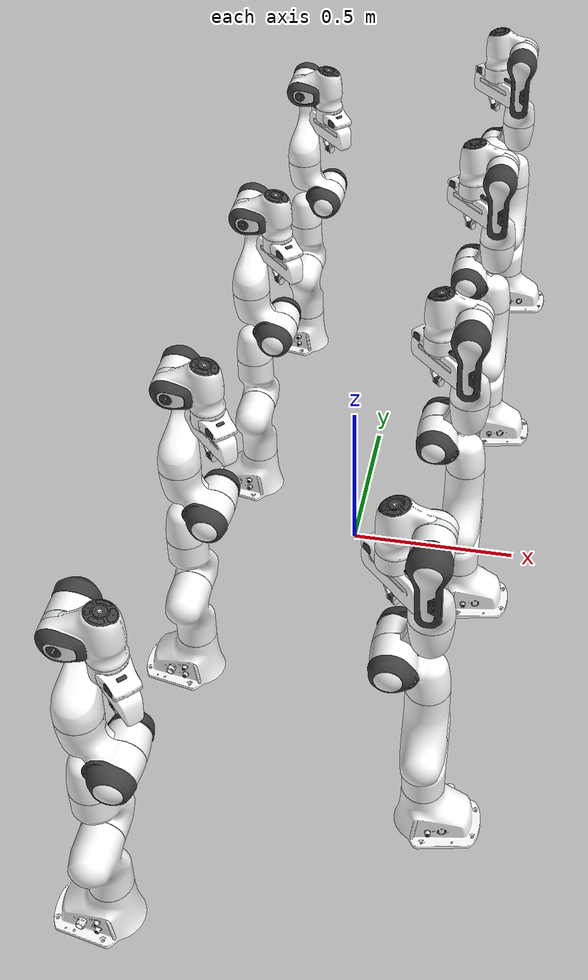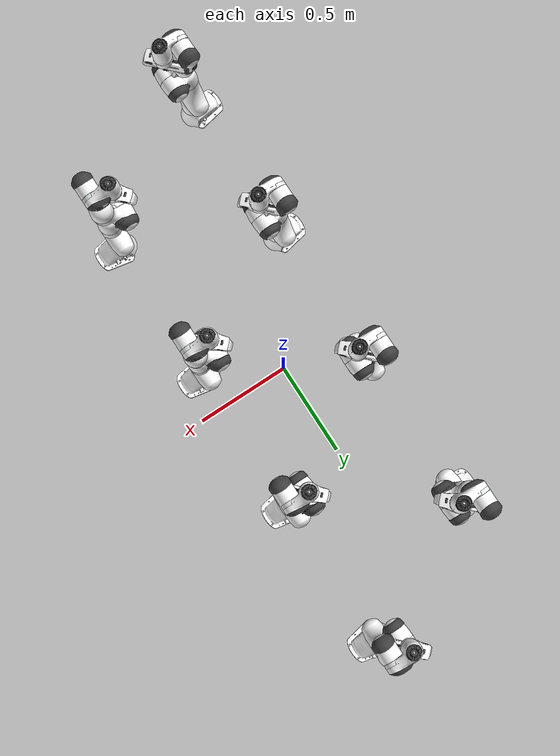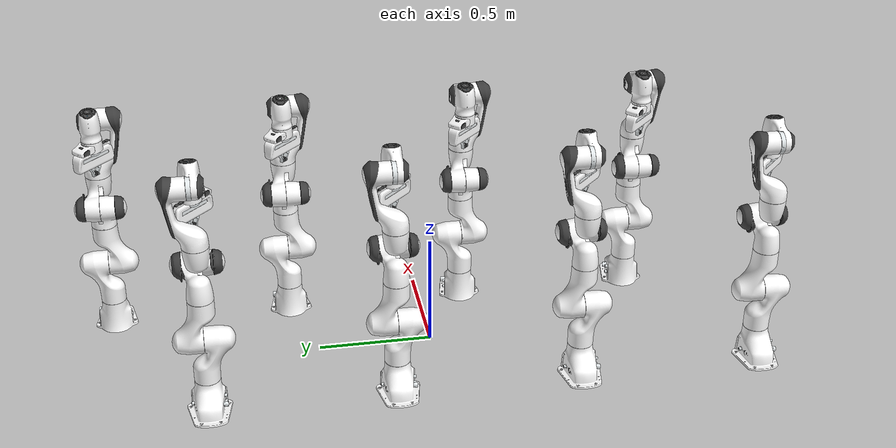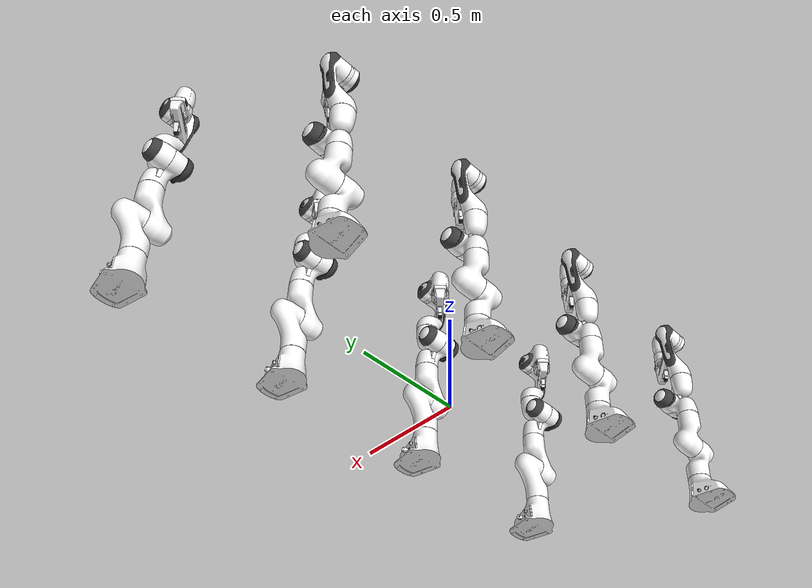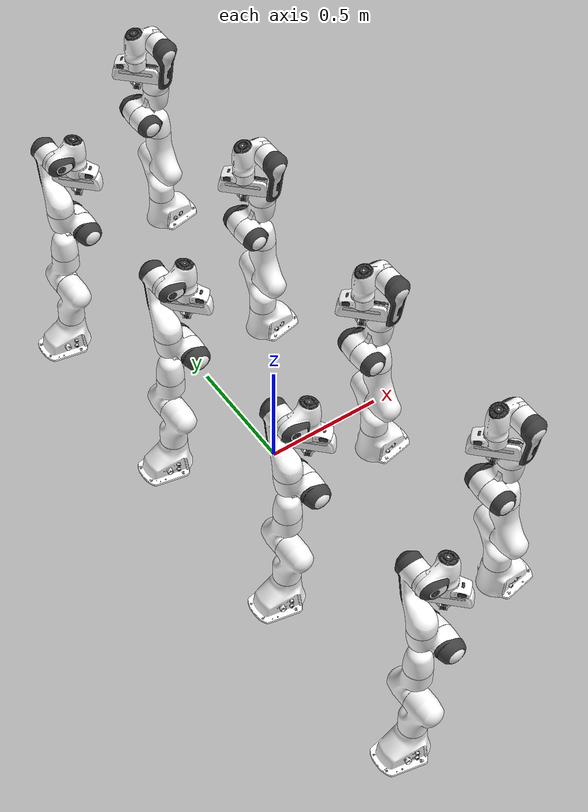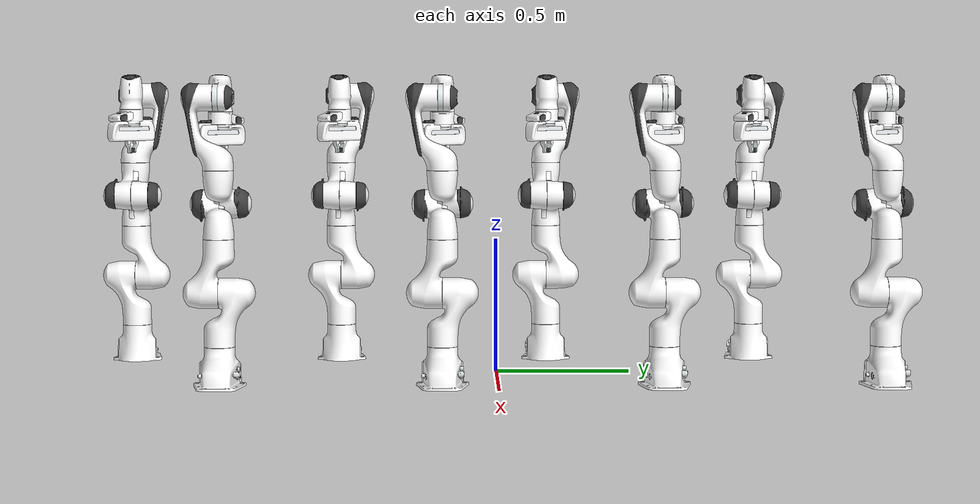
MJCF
<mujoco model="multi panda">
  <compiler angle="radian" meshdir="assets" autolimits="true"/>

  <option integrator="implicitfast"/>

  <default>
    <default class="panda">
      <material specular="0.5" shininess="0.25"/>
      <joint armature="0.1" damping="1" axis="0 0 1" range="-2.8973 2.8973"/>
      <general dyntype="none" biastype="affine" ctrlrange="-2.8973 2.8973" forcerange="-87 87"/>
      <default class="finger">
        <joint axis="0 1 0" type="slide" range="0 0.04"/>
      </default>

      <default class="visual">
        <geom type="mesh" contype="0" conaffinity="0" group="2"/>
      </default>
      <default class="collision">
        <geom type="mesh" group="3"/>
        <default class="fingertip_pad_collision_1">
          <geom type="box" size="0.0085 0.004 0.0085" pos="0 0.0055 0.0445"/>
        </default>
        <default class="fingertip_pad_collision_2">
          <geom type="box" size="0.003 0.002 0.003" pos="0.0055 0.002 0.05"/>
        </default>
        <default class="fingertip_pad_collision_3">
          <geom type="box" size="0.003 0.002 0.003" pos="-0.0055 0.002 0.05"/>
        </default>
        <default class="fingertip_pad_collision_4">
          <geom type="box" size="0.003 0.002 0.0035" pos="0.0055 0.002 0.0395"/>
        </default>
        <default class="fingertip_pad_collision_5">
          <geom type="box" size="0.003 0.002 0.0035" pos="-0.0055 0.002 0.0395"/>
        </default>
      </default>
    </default>
  </default>

  <asset>
    <material class="panda" name="white" rgba="1 1 1 1"/>
    <material class="panda" name="off_white" rgba="0.901961 0.921569 0.929412 1"/>
    <material class="panda" name="black" rgba="0.25 0.25 0.25 1"/>
    <material class="panda" name="green" rgba="0 1 0 1"/>
    <material class="panda" name="light_blue" rgba="0.039216 0.541176 0.780392 1"/>

    <!-- Collision meshes -->
    <mesh name="link0_c" file="link0.stl"/>
    <mesh name="link1_c" file="link1.stl"/>
    <mesh name="link2_c" file="link2.stl"/>
    <mesh name="link3_c" file="link3.stl"/>
    <mesh name="link4_c" file="link4.stl"/>
    <mesh name="link5_c0" file="link5_collision_0.obj"/>
    <mesh name="link5_c1" file="link5_collision_1.obj"/>
    <mesh name="link5_c2" file="link5_collision_2.obj"/>
    <mesh name="link6_c" file="link6.stl"/>
    <mesh name="link7_c" file="link7.stl"/>
    <mesh name="hand_c" file="hand.stl"/>

    <!-- Visual meshes (list shortened to avoid duplication) -->
    <mesh file="link0_0.obj"/>
    <mesh file="link0_1.obj"/>
    <mesh file="link0_2.obj"/>
    <mesh file="link0_3.obj"/>
    <mesh file="link0_4.obj"/>
    <mesh file="link0_5.obj"/>
    <mesh file="link0_7.obj"/>
    <mesh file="link0_8.obj"/>
    <mesh file="link0_9.obj"/>
    <mesh file="link0_10.obj"/>
    <mesh file="link0_11.obj"/>
    <mesh file="link1.obj"/>
    <mesh file="link2.obj"/>
    <mesh file="link3_0.obj"/>
    <mesh file="link3_1.obj"/>
    <mesh file="link3_2.obj"/>
    <mesh file="link3_3.obj"/>
    <mesh file="link4_0.obj"/>
    <mesh file="link4_1.obj"/>
    <mesh file="link4_2.obj"/>
    <mesh file="link4_3.obj"/>
    <mesh file="link5_0.obj"/>
    <mesh file="link5_1.obj"/>
    <mesh file="link5_2.obj"/>
    <mesh file="link6_0.obj"/>
    <mesh file="link6_1.obj"/>
    <mesh file="link6_2.obj"/>
    <mesh file="link6_3.obj"/>
    <mesh file="link6_4.obj"/>
    <mesh file="link6_5.obj"/>
    <mesh file="link6_6.obj"/>
    <mesh file="link6_7.obj"/>
    <mesh file="link6_8.obj"/>
    <mesh file="link6_9.obj"/>
    <mesh file="link6_10.obj"/>
    <mesh file="link6_11.obj"/>
    <mesh file="link6_12.obj"/>
    <mesh file="link6_13.obj"/>
    <mesh file="link6_14.obj"/>
    <mesh file="link6_15.obj"/>
    <mesh file="link6_16.obj"/>
    <mesh file="link7_0.obj"/>
    <mesh file="link7_1.obj"/>
    <mesh file="link7_2.obj"/>
    <mesh file="link7_3.obj"/>
    <mesh file="link7_4.obj"/>
    <mesh file="link7_5.obj"/>
    <mesh file="link7_6.obj"/>
    <mesh file="link7_7.obj"/>
    <mesh file="hand_0.obj"/>
    <mesh file="hand_1.obj"/>
    <mesh file="hand_2.obj"/>
    <mesh file="hand_3.obj"/>
    <mesh file="hand_4.obj"/>
    <mesh file="finger_0.obj"/>
    <mesh file="finger_1.obj"/>
  </asset>

  <!-- We'll spawn four robot instances by copying only the body subtrees and giving each instance a unique prefix. -->

  <visual>
    <headlight diffuse="0.6 0.6 0.6" ambient="0.3 0.3 0.3" specular="0 0 0"/>
    <rgba haze="0.15 0.25 0.35 1"/>
    <global azimuth="120" elevation="-20"/>
  </visual>

  <worldbody>
    <light pos="0 0 2" mode="trackcom"/>

    <!-- Arranged as two facing pairs with a zipper offset and a central work strip -->
    <!-- panda1: left column (pair 1,2), lowest y (alternate along y). X moved closer to center -->
    <body name="panda1_link0" childclass="panda" pos="-0.35 -0.60 0" quat="1 0 0 0">
      <inertial mass="0.629769" pos="-0.041018 -0.00014 0.049974" fullinertia="0.00315 0.00388 0.004285 8.2904e-7 0.00015 8.2299e-6"/>
      <geom mesh="link0_0" material="off_white" class="visual"/>
      <geom mesh="link0_1" material="black" class="visual"/>
      <geom mesh="link0_2" material="off_white" class="visual"/>
      <geom mesh="link0_3" material="black" class="visual"/>
      <geom mesh="link0_4" material="off_white" class="visual"/>
      <geom mesh="link0_5" material="black" class="visual"/>
      <geom mesh="link0_7" material="white" class="visual"/>
      <geom mesh="link0_8" material="white" class="visual"/>
      <geom mesh="link0_9" material="black" class="visual"/>
      <geom mesh="link0_10" material="off_white" class="visual"/>
      <geom mesh="link0_11" material="white" class="visual"/>
      <geom mesh="link0_c" class="collision"/>
      <body name="panda1_link1" pos="0 0 0.333">
        <inertial mass="4.970684" pos="0.003875 0.002081 -0.04762" fullinertia="0.70337 0.70661 0.0091170 -0.00013900 0.0067720 0.019169"/>
        <joint name="panda1_joint1"/>
        <geom material="white" mesh="link1" class="visual"/>
        <geom mesh="link1_c" class="collision"/>
        <body name="panda1_link2" quat="1 -1 0 0">
          <inertial mass="0.646926" pos="-0.003141 -0.02872 0.003495" fullinertia="0.0079620 2.8110e-2 2.5995e-2 -3.925e-3 1.0254e-2 7.04e-4"/>
          <joint name="panda1_joint2" range="-1.7628 1.7628"/>
          <geom material="white" mesh="link2" class="visual"/>
          <geom mesh="link2_c" class="collision"/>
          <body name="panda1_link3" pos="0 -0.316 0" quat="1 1 0 0">
            <joint name="panda1_joint3"/>
            <inertial mass="3.228604" pos="2.7518e-2 3.9252e-2 -6.6502e-2" fullinertia="3.7242e-2 3.6155e-2 1.083e-2 -4.761e-3 -1.1396e-2 -1.2805e-2"/>
            <geom mesh="link3_0" material="white" class="visual"/>
            <geom mesh="link3_1" material="white" class="visual"/>
            <geom mesh="link3_2" material="white" class="visual"/>
            <geom mesh="link3_3" material="black" class="visual"/>
            <geom mesh="link3_c" class="collision"/>
            <body name="panda1_link4" pos="0.0825 0 0" quat="1 1 0 0">
              <joint name="panda1_joint4" range="-3.0718 -0.0698"/>
              <inertial mass="3.587895" pos="-5.317e-2 1.04419e-1 2.7454e-2" fullinertia="2.5853e-2 1.9552e-2 2.8323e-2 7.796e-3 -1.332e-3 8.641e-3"/>
              <geom mesh="link4_0" material="white" class="visual"/>
              <geom mesh="link4_1" material="white" class="visual"/>
              <geom mesh="link4_2" material="black" class="visual"/>
              <geom mesh="link4_3" material="white" class="visual"/>
              <geom mesh="link4_c" class="collision"/>
              <body name="panda1_link5" pos="-0.0825 0.384 0" quat="1 -1 0 0">
                <joint name="panda1_joint5"/>
                <inertial mass="1.225946" pos="-1.1953e-2 4.1065e-2 -3.8437e-2" fullinertia="3.5549e-2 2.9474e-2 8.627e-3 -2.117e-3 -4.037e-3 2.29e-4"/>
                <geom mesh="link5_0" material="black" class="visual"/>
                <geom mesh="link5_1" material="white" class="visual"/>
                <geom mesh="link5_2" material="white" class="visual"/>
                <geom mesh="link5_c0" class="collision"/>
                <geom mesh="link5_c1" class="collision"/>
                <geom mesh="link5_c2" class="collision"/>
                <body name="panda1_link6" quat="1 1 0 0">
                  <joint name="panda1_joint6" range="-0.0175 3.7525"/>
                  <inertial mass="1.666555" pos="6.0149e-2 -1.4117e-2 -1.0517e-2" fullinertia="1.964e-3 4.354e-3 5.433e-3 1.09e-4 -1.158e-3 3.41e-4"/>
                  <geom mesh="link6_0" material="off_white" class="visual"/>
                  <geom mesh="link6_1" material="white" class="visual"/>
                  <geom mesh="link6_2" material="black" class="visual"/>
                  <geom mesh="link6_3" material="white" class="visual"/>
                  <geom mesh="link6_4" material="white" class="visual"/>
                  <geom mesh="link6_5" material="white" class="visual"/>
                  <geom mesh="link6_6" material="white" class="visual"/>
                  <geom mesh="link6_7" material="light_blue" class="visual"/>
                  <geom mesh="link6_8" material="light_blue" class="visual"/>
                  <geom mesh="link6_9" material="black" class="visual"/>
                  <geom mesh="link6_10" material="black" class="visual"/>
                  <geom mesh="link6_11" material="white" class="visual"/>
                  <geom mesh="link6_12" material="green" class="visual"/>
                  <geom mesh="link6_13" material="white" class="visual"/>
                  <geom mesh="link6_14" material="black" class="visual"/>
                  <geom mesh="link6_15" material="black" class="visual"/>
                  <geom mesh="link6_16" material="white" class="visual"/>
                  <geom mesh="link6_c" class="collision"/>
                  <body name="panda1_link7" pos="0.088 0 0" quat="1 1 0 0">
                    <joint name="panda1_joint7"/>
                    <inertial mass="7.35522e-01" pos="1.0517e-2 -4.252e-3 6.1597e-2" fullinertia="1.2516e-2 1.0027e-2 4.815e-3 -4.28e-4 -1.196e-3 -7.41e-4"/>
                    <geom mesh="link7_0" material="white" class="visual"/>
                    <geom mesh="link7_1" material="black" class="visual"/>
                    <geom mesh="link7_2" material="black" class="visual"/>
                    <geom mesh="link7_3" material="black" class="visual"/>
                    <geom mesh="link7_4" material="black" class="visual"/>
                    <geom mesh="link7_5" material="black" class="visual"/>
                    <geom mesh="link7_6" material="black" class="visual"/>
                    <geom mesh="link7_7" material="white" class="visual"/>
                    <geom mesh="link7_c" class="collision"/>
                    <body name="panda1_hand" pos="0 0 0.107" quat="0.9238795 0 0 -0.3826834">
                      <inertial mass="0.73" pos="-0.01 0 0.03" diaginertia="0.001 0.0025 0.0017"/>
                      <geom mesh="hand_0" material="off_white" class="visual"/>
                      <geom mesh="hand_1" material="black" class="visual"/>
                      <geom mesh="hand_2" material="black" class="visual"/>
                      <geom mesh="hand_3" material="white" class="visual"/>
                      <geom mesh="hand_4" material="off_white" class="visual"/>
                      <geom mesh="hand_c" class="collision"/>
                      <body name="panda1_left_finger" pos="0 0 0.0584">
                        <inertial mass="0.015" pos="0 0 0" diaginertia="2.375e-6 2.375e-6 7.5e-7"/>
                        <joint name="panda1_finger_joint1" class="finger"/>
                        <geom mesh="finger_0" material="off_white" class="visual"/>
                        <geom mesh="finger_1" material="black" class="visual"/>
                        <geom mesh="finger_0" class="collision"/>
                        <geom class="fingertip_pad_collision_1"/>
                        <geom class="fingertip_pad_collision_2"/>
                        <geom class="fingertip_pad_collision_3"/>
                        <geom class="fingertip_pad_collision_4"/>
                        <geom class="fingertip_pad_collision_5"/>
                      </body>
                      <body name="panda1_right_finger" pos="0 0 0.0584" quat="0 0 0 1">
                        <inertial mass="0.015" pos="0 0 0" diaginertia="2.375e-6 2.375e-6 7.5e-7"/>
                        <joint name="panda1_finger_joint2" class="finger"/>
                        <geom mesh="finger_0" material="off_white" class="visual"/>
                        <geom mesh="finger_1" material="black" class="visual"/>
                        <geom mesh="finger_0" class="collision"/>
                        <geom class="fingertip_pad_collision_1"/>
                        <geom class="fingertip_pad_collision_2"/>
                        <geom class="fingertip_pad_collision_3"/>
                        <geom class="fingertip_pad_collision_4"/>
                        <geom class="fingertip_pad_collision_5"/>
                      </body>
                    </body>
                  </body>
                </body>
              </body>
            </body>
          </body>
        </body>
      </body>
    </body>

    <!-- panda2: left column (pair 1,2), higher y. X moved closer to center -->
    <body name="panda2_link0" childclass="panda" pos="-0.35 0.20 0" quat="1 0 0 0">
      <inertial mass="0.629769" pos="-0.041018 -0.00014 0.049974" fullinertia="0.00315 0.00388 0.004285 8.2904e-7 0.00015 8.2299e-6"/>
      <geom mesh="link0_0" material="off_white" class="visual"/>
      <geom mesh="link0_1" material="black" class="visual"/>
      <geom mesh="link0_2" material="off_white" class="visual"/>
      <geom mesh="link0_3" material="black" class="visual"/>
      <geom mesh="link0_4" material="off_white" class="visual"/>
      <geom mesh="link0_5" material="black" class="visual"/>
      <geom mesh="link0_7" material="white" class="visual"/>
      <geom mesh="link0_8" material="white" class="visual"/>
      <geom mesh="link0_9" material="black" class="visual"/>
      <geom mesh="link0_10" material="off_white" class="visual"/>
      <geom mesh="link0_11" material="white" class="visual"/>
      <geom mesh="link0_c" class="collision"/>
      <body name="panda2_link1" pos="0 0 0.333">
        <inertial mass="4.970684" pos="0.003875 0.002081 -0.04762" fullinertia="0.70337 0.70661 0.0091170 -0.00013900 0.0067720 0.019169"/>
        <joint name="panda2_joint1"/>
        <geom material="white" mesh="link1" class="visual"/>
        <geom mesh="link1_c" class="collision"/>
        <body name="panda2_link2" quat="1 -1 0 0">
          <inertial mass="0.646926" pos="-0.003141 -0.02872 0.003495" fullinertia="0.0079620 2.8110e-2 2.5995e-2 -3.925e-3 1.0254e-2 7.04e-4"/>
          <joint name="panda2_joint2" range="-1.7628 1.7628"/>
          <geom material="white" mesh="link2" class="visual"/>
          <geom mesh="link2_c" class="collision"/>
          <body name="panda2_link3" pos="0 -0.316 0" quat="1 1 0 0">
            <joint name="panda2_joint3"/>
            <inertial mass="3.228604" pos="2.7518e-2 3.9252e-2 -6.6502e-2" fullinertia="3.7242e-2 3.6155e-2 1.083e-2 -4.761e-3 -1.1396e-2 -1.2805e-2"/>
            <geom mesh="link3_0" material="white" class="visual"/>
            <geom mesh="link3_1" material="white" class="visual"/>
            <geom mesh="link3_2" material="white" class="visual"/>
            <geom mesh="link3_3" material="black" class="visual"/>
            <geom mesh="link3_c" class="collision"/>
            <body name="panda2_link4" pos="0.0825 0 0" quat="1 1 0 0">
              <joint name="panda2_joint4" range="-3.0718 -0.0698"/>
              <inertial mass="3.587895" pos="-5.317e-2 1.04419e-1 2.7454e-2" fullinertia="2.5853e-2 1.9552e-2 2.8323e-2 7.796e-3 -1.332e-3 8.641e-3"/>
              <geom mesh="link4_0" material="white" class="visual"/>
              <geom mesh="link4_1" material="white" class="visual"/>
              <geom mesh="link4_2" material="black" class="visual"/>
              <geom mesh="link4_3" material="white" class="visual"/>
              <geom mesh="link4_c" class="collision"/>
              <body name="panda2_link5" pos="-0.0825 0.384 0" quat="1 -1 0 0">
                <joint name="panda2_joint5"/>
                <inertial mass="1.225946" pos="-1.1953e-2 4.1065e-2 -3.8437e-2" fullinertia="3.5549e-2 2.9474e-2 8.627e-3 -2.117e-3 -4.037e-3 2.29e-4"/>
                <geom mesh="link5_0" material="black" class="visual"/>
                <geom mesh="link5_1" material="white" class="visual"/>
                <geom mesh="link5_2" material="white" class="visual"/>
                <geom mesh="link5_c0" class="collision"/>
                <geom mesh="link5_c1" class="collision"/>
                <geom mesh="link5_c2" class="collision"/>
                <body name="panda2_link6" quat="1 1 0 0">
                  <joint name="panda2_joint6" range="-0.0175 3.7525"/>
                  <inertial mass="1.666555" pos="6.0149e-2 -1.4117e-2 -1.0517e-2" fullinertia="1.964e-3 4.354e-3 5.433e-3 1.09e-4 -1.158e-3 3.41e-4"/>
                  <geom mesh="link6_0" material="off_white" class="visual"/>
                  <geom mesh="link6_1" material="white" class="visual"/>
                  <geom mesh="link6_2" material="black" class="visual"/>
                  <geom mesh="link6_3" material="white" class="visual"/>
                  <geom mesh="link6_4" material="white" class="visual"/>
                  <geom mesh="link6_5" material="white" class="visual"/>
                  <geom mesh="link6_6" material="white" class="visual"/>
                  <geom mesh="link6_7" material="light_blue" class="visual"/>
                  <geom mesh="link6_8" material="light_blue" class="visual"/>
                  <geom mesh="link6_9" material="black" class="visual"/>
                  <geom mesh="link6_10" material="black" class="visual"/>
                  <geom mesh="link6_11" material="white" class="visual"/>
                  <geom mesh="link6_12" material="green" class="visual"/>
                  <geom mesh="link6_13" material="white" class="visual"/>
                  <geom mesh="link6_14" material="black" class="visual"/>
                  <geom mesh="link6_15" material="black" class="visual"/>
                  <geom mesh="link6_16" material="white" class="visual"/>
                  <geom mesh="link6_c" class="collision"/>
                  <body name="panda2_link7" pos="0.088 0 0" quat="1 1 0 0">
                    <joint name="panda2_joint7"/>
                    <inertial mass="7.35522e-01" pos="1.0517e-2 -4.252e-3 6.1597e-2" fullinertia="1.2516e-2 1.0027e-2 4.815e-3 -4.28e-4 -1.196e-3 -7.41e-4"/>
                    <geom mesh="link7_0" material="white" class="visual"/>
                    <geom mesh="link7_1" material="black" class="visual"/>
                    <geom mesh="link7_2" material="black" class="visual"/>
                    <geom mesh="link7_3" material="black" class="visual"/>
                    <geom mesh="link7_4" material="black" class="visual"/>
                    <geom mesh="link7_5" material="black" class="visual"/>
                    <geom mesh="link7_6" material="black" class="visual"/>
                    <geom mesh="link7_7" material="white" class="visual"/>
                    <geom mesh="link7_c" class="collision"/>
                    <body name="panda2_hand" pos="0 0 0.107" quat="0.9238795 0 0 -0.3826834">
                      <inertial mass="0.73" pos="-0.01 0 0.03" diaginertia="0.001 0.0025 0.0017"/>
                      <geom mesh="hand_0" material="off_white" class="visual"/>
                      <geom mesh="hand_1" material="black" class="visual"/>
                      <geom mesh="hand_2" material="black" class="visual"/>
                      <geom mesh="hand_3" material="white" class="visual"/>
                      <geom mesh="hand_4" material="off_white" class="visual"/>
                      <geom mesh="hand_c" class="collision"/>
                      <body name="panda2_left_finger" pos="0 0 0.0584">
                        <inertial mass="0.015" pos="0 0 0" diaginertia="2.375e-6 2.375e-6 7.5e-7"/>
                        <joint name="panda2_finger_joint1" class="finger"/>
                        <geom mesh="finger_0" material="off_white" class="visual"/>
                        <geom mesh="finger_1" material="black" class="visual"/>
                        <geom mesh="finger_0" class="collision"/>
                        <geom class="fingertip_pad_collision_1"/>
                        <geom class="fingertip_pad_collision_2"/>
                        <geom class="fingertip_pad_collision_3"/>
                        <geom class="fingertip_pad_collision_4"/>
                        <geom class="fingertip_pad_collision_5"/>
                      </body>
                      <body name="panda2_right_finger" pos="0 0 0.0584" quat="0 0 0 1">
                        <inertial mass="0.015" pos="0 0 0" diaginertia="2.375e-6 2.375e-6 7.5e-7"/>
                        <joint name="panda2_finger_joint2" class="finger"/>
                        <geom mesh="finger_0" material="off_white" class="visual"/>
                        <geom mesh="finger_1" material="black" class="visual"/>
                        <geom mesh="finger_0" class="collision"/>
                        <geom class="fingertip_pad_collision_1"/>
                        <geom class="fingertip_pad_collision_2"/>
                        <geom class="fingertip_pad_collision_3"/>
                        <geom class="fingertip_pad_collision_4"/>
                        <geom class="fingertip_pad_collision_5"/>
                      </body>
                    </body>
                  </body>
                </body>
              </body>
            </body>
          </body>
        </body>
      </body>
    </body>

    <!-- panda3: right column (pair 3,4), lower y (alternate along y). X moved closer to center -->
    <body name="panda3_link0" childclass="panda" pos="0.35 -0.20 0" quat="0 0 0 1">
      <inertial mass="0.629769" pos="-0.041018 -0.00014 0.049974" fullinertia="0.00315 0.00388 0.004285 8.2904e-7 0.00015 8.2299e-6"/>
      <geom mesh="link0_0" material="off_white" class="visual"/>
      <geom mesh="link0_1" material="black" class="visual"/>
      <geom mesh="link0_2" material="off_white" class="visual"/>
      <geom mesh="link0_3" material="black" class="visual"/>
      <geom mesh="link0_4" material="off_white" class="visual"/>
      <geom mesh="link0_5" material="black" class="visual"/>
      <geom mesh="link0_7" material="white" class="visual"/>
      <geom mesh="link0_8" material="white" class="visual"/>
      <geom mesh="link0_9" material="black" class="visual"/>
      <geom mesh="link0_10" material="off_white" class="visual"/>
      <geom mesh="link0_11" material="white" class="visual"/>
      <geom mesh="link0_c" class="collision"/>
      <body name="panda3_link1" pos="0 0 0.333">
        <inertial mass="4.970684" pos="0.003875 0.002081 -0.04762" fullinertia="0.70337 0.70661 0.0091170 -0.00013900 0.0067720 0.019169"/>
        <joint name="panda3_joint1"/>
        <geom material="white" mesh="link1" class="visual"/>
        <geom mesh="link1_c" class="collision"/>
        <body name="panda3_link2" quat="1 -1 0 0">
          <inertial mass="0.646926" pos="-0.003141 -0.02872 0.003495" fullinertia="0.0079620 2.8110e-2 2.5995e-2 -3.925e-3 1.0254e-2 7.04e-4"/>
          <joint name="panda3_joint2" range="-1.7628 1.7628"/>
          <geom material="white" mesh="link2" class="visual"/>
          <geom mesh="link2_c" class="collision"/>
          <body name="panda3_link3" pos="0 -0.316 0" quat="1 1 0 0">
            <joint name="panda3_joint3"/>
            <inertial mass="3.228604" pos="2.7518e-2 3.9252e-2 -6.6502e-2" fullinertia="3.7242e-2 3.6155e-2 1.083e-2 -4.761e-3 -1.1396e-2 -1.2805e-2"/>
            <geom mesh="link3_0" material="white" class="visual"/>
            <geom mesh="link3_1" material="white" class="visual"/>
            <geom mesh="link3_2" material="white" class="visual"/>
            <geom mesh="link3_3" material="black" class="visual"/>
            <geom mesh="link3_c" class="collision"/>
            <body name="panda3_link4" pos="0.0825 0 0" quat="1 1 0 0">
              <joint name="panda3_joint4" range="-3.0718 -0.0698"/>
              <inertial mass="3.587895" pos="-5.317e-2 1.04419e-1 2.7454e-2" fullinertia="2.5853e-2 1.9552e-2 2.8323e-2 7.796e-3 -1.332e-3 8.641e-3"/>
              <geom mesh="link4_0" material="white" class="visual"/>
              <geom mesh="link4_1" material="white" class="visual"/>
              <geom mesh="link4_2" material="black" class="visual"/>
              <geom mesh="link4_3" material="white" class="visual"/>
              <geom mesh="link4_c" class="collision"/>
              <body name="panda3_link5" pos="-0.0825 0.384 0" quat="1 -1 0 0">
                <joint name="panda3_joint5"/>
                <inertial mass="1.225946" pos="-1.1953e-2 4.1065e-2 -3.8437e-2" fullinertia="3.5549e-2 2.9474e-2 8.627e-3 -2.117e-3 -4.037e-3 2.29e-4"/>
                <geom mesh="link5_0" material="black" class="visual"/>
                <geom mesh="link5_1" material="white" class="visual"/>
                <geom mesh="link5_2" material="white" class="visual"/>
                <geom mesh="link5_c0" class="collision"/>
                <geom mesh="link5_c1" class="collision"/>
                <geom mesh="link5_c2" class="collision"/>
                <body name="panda3_link6" quat="1 1 0 0">
                  <joint name="panda3_joint6" range="-0.0175 3.7525"/>
                  <inertial mass="1.666555" pos="6.0149e-2 -1.4117e-2 -1.0517e-2" fullinertia="1.964e-3 4.354e-3 5.433e-3 1.09e-4 -1.158e-3 3.41e-4"/>
                  <geom mesh="link6_0" material="off_white" class="visual"/>
                  <geom mesh="link6_1" material="white" class="visual"/>
                  <geom mesh="link6_2" material="black" class="visual"/>
                  <geom mesh="link6_3" material="white" class="visual"/>
                  <geom mesh="link6_4" material="white" class="visual"/>
                  <geom mesh="link6_5" material="white" class="visual"/>
                  <geom mesh="link6_6" material="white" class="visual"/>
                  <geom mesh="link6_7" material="light_blue" class="visual"/>
                  <geom mesh="link6_8" material="light_blue" class="visual"/>
                  <geom mesh="link6_9" material="black" class="visual"/>
                  <geom mesh="link6_10" material="black" class="visual"/>
                  <geom mesh="link6_11" material="white" class="visual"/>
                  <geom mesh="link6_12" material="green" class="visual"/>
                  <geom mesh="link6_13" material="white" class="visual"/>
                  <geom mesh="link6_14" material="black" class="visual"/>
                  <geom mesh="link6_15" material="black" class="visual"/>
                  <geom mesh="link6_16" material="white" class="visual"/>
                  <geom mesh="link6_c" class="collision"/>
                  <body name="panda3_link7" pos="0.088 0 0" quat="1 1 0 0">
                    <joint name="panda3_joint7"/>
                    <inertial mass="7.35522e-01" pos="1.0517e-2 -4.252e-3 6.1597e-2" fullinertia="1.2516e-2 1.0027e-2 4.815e-3 -4.28e-4 -1.196e-3 -7.41e-4"/>
                    <geom mesh="link7_0" material="white" class="visual"/>
                    <geom mesh="link7_1" material="black" class="visual"/>
                    <geom mesh="link7_2" material="black" class="visual"/>
                    <geom mesh="link7_3" material="black" class="visual"/>
                    <geom mesh="link7_4" material="black" class="visual"/>
                    <geom mesh="link7_5" material="black" class="visual"/>
                    <geom mesh="link7_6" material="black" class="visual"/>
                    <geom mesh="link7_7" material="white" class="visual"/>
                    <geom mesh="link7_c" class="collision"/>
                    <body name="panda3_hand" pos="0 0 0.107" quat="0.9238795 0 0 -0.3826834">
                      <inertial mass="0.73" pos="-0.01 0 0.03" diaginertia="0.001 0.0025 0.0017"/>
                      <geom mesh="hand_0" material="off_white" class="visual"/>
                      <geom mesh="hand_1" material="black" class="visual"/>
                      <geom mesh="hand_2" material="black" class="visual"/>
                      <geom mesh="hand_3" material="white" class="visual"/>
                      <geom mesh="hand_4" material="off_white" class="visual"/>
                      <geom mesh="hand_c" class="collision"/>
                      <body name="panda3_left_finger" pos="0 0 0.0584">
                        <inertial mass="0.015" pos="0 0 0" diaginertia="2.375e-6 2.375e-6 7.5e-7"/>
                        <joint name="panda3_finger_joint1" class="finger"/>
                        <geom mesh="finger_0" material="off_white" class="visual"/>
                        <geom mesh="finger_1" material="black" class="visual"/>
                        <geom mesh="finger_0" class="collision"/>
                        <geom class="fingertip_pad_collision_1"/>
                        <geom class="fingertip_pad_collision_2"/>
                        <geom class="fingertip_pad_collision_3"/>
                        <geom class="fingertip_pad_collision_4"/>
                        <geom class="fingertip_pad_collision_5"/>
                      </body>
                      <body name="panda3_right_finger" pos="0 0 0.0584" quat="0 0 0 1">
                        <inertial mass="0.015" pos="0 0 0" diaginertia="2.375e-6 2.375e-6 7.5e-7"/>
                        <joint name="panda3_finger_joint2" class="finger"/>
                        <geom mesh="finger_0" material="off_white" class="visual"/>
                        <geom mesh="finger_1" material="black" class="visual"/>
                        <geom mesh="finger_0" class="collision"/>
                        <geom class="fingertip_pad_collision_1"/>
                        <geom class="fingertip_pad_collision_2"/>
                        <geom class="fingertip_pad_collision_3"/>
                        <geom class="fingertip_pad_collision_4"/>
                        <geom class="fingertip_pad_collision_5"/>
                      </body>
                    </body>
                  </body>
                </body>
              </body>
            </body>
          </body>
        </body>
      </body>
    </body>

    <!-- panda4: right column (pair 3,4), highest y. X moved closer to center -->
    <body name="panda4_link0" childclass="panda" pos="0.35 0.60 0" quat="0 0 0 1">
      <inertial mass="0.629769" pos="-0.041018 -0.00014 0.049974" fullinertia="0.00315 0.00388 0.004285 8.2904e-7 0.00015 8.2299e-6"/>
      <geom mesh="link0_0" material="off_white" class="visual"/>
      <geom mesh="link0_1" material="black" class="visual"/>
      <geom mesh="link0_2" material="off_white" class="visual"/>
      <geom mesh="link0_3" material="black" class="visual"/>
      <geom mesh="link0_4" material="off_white" class="visual"/>
      <geom mesh="link0_5" material="black" class="visual"/>
      <geom mesh="link0_7" material="white" class="visual"/>
      <geom mesh="link0_8" material="white" class="visual"/>
      <geom mesh="link0_9" material="black" class="visual"/>
      <geom mesh="link0_10" material="off_white" class="visual"/>
      <geom mesh="link0_11" material="white" class="visual"/>
      <geom mesh="link0_c" class="collision"/>
      <body name="panda4_link1" pos="0 0 0.333">
        <inertial mass="4.970684" pos="0.003875 0.002081 -0.04762" fullinertia="0.70337 0.70661 0.0091170 -0.00013900 0.0067720 0.019169"/>
        <joint name="panda4_joint1"/>
        <geom material="white" mesh="link1" class="visual"/>
        <geom mesh="link1_c" class="collision"/>
        <body name="panda4_link2" quat="1 -1 0 0">
          <inertial mass="0.646926" pos="-0.003141 -0.02872 0.003495" fullinertia="0.0079620 2.8110e-2 2.5995e-2 -3.925e-3 1.0254e-2 7.04e-4"/>
          <joint name="panda4_joint2" range="-1.7628 1.7628"/>
          <geom material="white" mesh="link2" class="visual"/>
          <geom mesh="link2_c" class="collision"/>
          <body name="panda4_link3" pos="0 -0.316 0" quat="1 1 0 0">
            <joint name="panda4_joint3"/>
            <inertial mass="3.228604" pos="2.7518e-2 3.9252e-2 -6.6502e-2" fullinertia="3.7242e-2 3.6155e-2 1.083e-2 -4.761e-3 -1.1396e-2 -1.2805e-2"/>
            <geom mesh="link3_0" material="white" class="visual"/>
            <geom mesh="link3_1" material="white" class="visual"/>
            <geom mesh="link3_2" material="white" class="visual"/>
            <geom mesh="link3_3" material="black" class="visual"/>
            <geom mesh="link3_c" class="collision"/>
            <body name="panda4_link4" pos="0.0825 0 0" quat="1 1 0 0">
              <joint name="panda4_joint4" range="-3.0718 -0.0698"/>
              <inertial mass="3.587895" pos="-5.317e-2 1.04419e-1 2.7454e-2" fullinertia="2.5853e-2 1.9552e-2 2.8323e-2 7.796e-3 -1.332e-3 8.641e-3"/>
              <geom mesh="link4_0" material="white" class="visual"/>
              <geom mesh="link4_1" material="white" class="visual"/>
              <geom mesh="link4_2" material="black" class="visual"/>
              <geom mesh="link4_3" material="white" class="visual"/>
              <geom mesh="link4_c" class="collision"/>
              <body name="panda4_link5" pos="-0.0825 0.384 0" quat="1 -1 0 0">
                <joint name="panda4_joint5"/>
                <inertial mass="1.225946" pos="-1.1953e-2 4.1065e-2 -3.8437e-2" fullinertia="3.5549e-2 2.9474e-2 8.627e-3 -2.117e-3 -4.037e-3 2.29e-4"/>
                <geom mesh="link5_0" material="black" class="visual"/>
                <geom mesh="link5_1" material="white" class="visual"/>
                <geom mesh="link5_2" material="white" class="visual"/>
                <geom mesh="link5_c0" class="collision"/>
                <geom mesh="link5_c1" class="collision"/>
                <geom mesh="link5_c2" class="collision"/>
                <body name="panda4_link6" quat="1 1 0 0">
                  <joint name="panda4_joint6" range="-0.0175 3.7525"/>
                  <inertial mass="1.666555" pos="6.0149e-2 -1.4117e-2 -1.0517e-2" fullinertia="1.964e-3 4.354e-3 5.433e-3 1.09e-4 -1.158e-3 3.41e-4"/>
                  <geom mesh="link6_0" material="off_white" class="visual"/>
                  <geom mesh="link6_1" material="white" class="visual"/>
                  <geom mesh="link6_2" material="black" class="visual"/>
                  <geom mesh="link6_3" material="white" class="visual"/>
                  <geom mesh="link6_4" material="white" class="visual"/>
                  <geom mesh="link6_5" material="white" class="visual"/>
                  <geom mesh="link6_6" material="white" class="visual"/>
                  <geom mesh="link6_7" material="light_blue" class="visual"/>
                  <geom mesh="link6_8" material="light_blue" class="visual"/>
                  <geom mesh="link6_9" material="black" class="visual"/>
                  <geom mesh="link6_10" material="black" class="visual"/>
                  <geom mesh="link6_11" material="white" class="visual"/>
                  <geom mesh="link6_12" material="green" class="visual"/>
                  <geom mesh="link6_13" material="white" class="visual"/>
                  <geom mesh="link6_14" material="black" class="visual"/>
                  <geom mesh="link6_15" material="black" class="visual"/>
                  <geom mesh="link6_16" material="white" class="visual"/>
                  <geom mesh="link6_c" class="collision"/>
                  <body name="panda4_link7" pos="0.088 0 0" quat="1 1 0 0">
                    <joint name="panda4_joint7"/>
                    <inertial mass="7.35522e-01" pos="1.0517e-2 -4.252e-3 6.1597e-2" fullinertia="1.2516e-2 1.0027e-2 4.815e-3 -4.28e-4 -1.196e-3 -7.41e-4"/>
                    <geom mesh="link7_0" material="white" class="visual"/>
                    <geom mesh="link7_1" material="black" class="visual"/>
                    <geom mesh="link7_2" material="black" class="visual"/>
                    <geom mesh="link7_3" material="black" class="visual"/>
                    <geom mesh="link7_4" material="black" class="visual"/>
                    <geom mesh="link7_5" material="black" class="visual"/>
                    <geom mesh="link7_6" material="black" class="visual"/>
                    <geom mesh="link7_7" material="white" class="visual"/>
                    <geom mesh="link7_c" class="collision"/>
                    <body name="panda4_hand" pos="0 0 0.107" quat="0.9238795 0 0 -0.3826834">
                      <inertial mass="0.73" pos="-0.01 0 0.03" diaginertia="0.001 0.0025 0.0017"/>
                      <geom mesh="hand_0" material="off_white" class="visual"/>
                      <geom mesh="hand_1" material="black" class="visual"/>
                      <geom mesh="hand_2" material="black" class="visual"/>
                      <geom mesh="hand_3" material="white" class="visual"/>
                      <geom mesh="hand_4" material="off_white" class="visual"/>
                      <geom mesh="hand_c" class="collision"/>
                      <body name="panda4_left_finger" pos="0 0 0.0584">
                        <inertial mass="0.015" pos="0 0 0" diaginertia="2.375e-6 2.375e-6 7.5e-7"/>
                        <joint name="panda4_finger_joint1" class="finger"/>
                        <geom mesh="finger_0" material="off_white" class="visual"/>
                        <geom mesh="finger_1" material="black" class="visual"/>
                        <geom mesh="finger_0" class="collision"/>
                        <geom class="fingertip_pad_collision_1"/>
                        <geom class="fingertip_pad_collision_2"/>
                        <geom class="fingertip_pad_collision_3"/>
                        <geom class="fingertip_pad_collision_4"/>
                        <geom class="fingertip_pad_collision_5"/>
                      </body>
                      <body name="panda4_right_finger" pos="0 0 0.0584" quat="0 0 0 1">
                        <inertial mass="0.015" pos="0 0 0" diaginertia="2.375e-6 2.375e-6 7.5e-7"/>
                        <joint name="panda4_finger_joint2" class="finger"/>
                        <geom mesh="finger_0" material="off_white" class="visual"/>
                        <geom mesh="finger_1" material="black" class="visual"/>
                        <geom mesh="finger_0" class="collision"/>
                        <geom class="fingertip_pad_collision_1"/>
                        <geom class="fingertip_pad_collision_2"/>
                        <geom class="fingertip_pad_collision_3"/>
                        <geom class="fingertip_pad_collision_4"/>
                        <geom class="fingertip_pad_collision_5"/>
                      </body>
                    </body>
                  </body>
                </body>
              </body>
            </body>
          </body>
        </body>
      </body>
    </body>

    <!-- Second set of 4 arms, shifted +10m in x -->
    <body name="panda5_link0" childclass="panda" pos="-0.35 -1.4 0" quat="1 0 0 0">
      <inertial mass="0.629769" pos="-0.041018 -0.00014 0.049974" fullinertia="0.00315 0.00388 0.004285 8.2904e-7 0.00015 8.2299e-6"/>
      <geom mesh="link0_0" material="off_white" class="visual"/>
      <geom mesh="link0_1" material="black" class="visual"/>
      <geom mesh="link0_2" material="off_white" class="visual"/>
      <geom mesh="link0_3" material="black" class="visual"/>
      <geom mesh="link0_4" material="off_white" class="visual"/>
      <geom mesh="link0_5" material="black" class="visual"/>
      <geom mesh="link0_7" material="white" class="visual"/>
      <geom mesh="link0_8" material="white" class="visual"/>
      <geom mesh="link0_9" material="black" class="visual"/>
      <geom mesh="link0_10" material="off_white" class="visual"/>
      <geom mesh="link0_11" material="white" class="visual"/>
      <geom mesh="link0_c" class="collision"/>
      <body name="panda5_link1" pos="0 0 0.333">
        <inertial mass="4.970684" pos="0.003875 0.002081 -0.04762" fullinertia="0.70337 0.70661 0.0091170 -0.00013900 0.0067720 0.019169"/>
        <joint name="panda5_joint1"/>
        <geom material="white" mesh="link1" class="visual"/>
        <geom mesh="link1_c" class="collision"/>
        <body name="panda5_link2" quat="1 -1 0 0">
          <inertial mass="0.646926" pos="-0.003141 -0.02872 0.003495" fullinertia="0.0079620 2.8110e-2 2.5995e-2 -3.925e-3 1.0254e-2 7.04e-4"/>
          <joint name="panda5_joint2" range="-1.7628 1.7628"/>
          <geom material="white" mesh="link2" class="visual"/>
          <geom mesh="link2_c" class="collision"/>
          <body name="panda5_link3" pos="0 -0.316 0" quat="1 1 0 0">
            <joint name="panda5_joint3"/>
            <inertial mass="3.228604" pos="2.7518e-2 3.9252e-2 -6.6502e-2" fullinertia="3.7242e-2 3.6155e-2 1.083e-2 -4.761e-3 -1.1396e-2 -1.2805e-2"/>
            <geom mesh="link3_0" material="white" class="visual"/>
            <geom mesh="link3_1" material="white" class="visual"/>
            <geom mesh="link3_2" material="white" class="visual"/>
            <geom mesh="link3_3" material="black" class="visual"/>
            <geom mesh="link3_c" class="collision"/>
            <body name="panda5_link4" pos="0.0825 0 0" quat="1 1 0 0">
              <joint name="panda5_joint4" range="-3.0718 -0.0698"/>
              <inertial mass="3.587895" pos="-5.317e-2 1.04419e-1 2.7454e-2" fullinertia="2.5853e-2 1.9552e-2 2.8323e-2 7.796e-3 -1.332e-3 8.641e-3"/>
              <geom mesh="link4_0" material="white" class="visual"/>
              <geom mesh="link4_1" material="white" class="visual"/>
              <geom mesh="link4_2" material="black" class="visual"/>
              <geom mesh="link4_3" material="white" class="visual"/>
              <geom mesh="link4_c" class="collision"/>
              <body name="panda5_link5" pos="-0.0825 0.384 0" quat="1 -1 0 0">
                <joint name="panda5_joint5"/>
                <inertial mass="1.225946" pos="-1.1953e-2 4.1065e-2 -3.8437e-2" fullinertia="3.5549e-2 2.9474e-2 8.627e-3 -2.117e-3 -4.037e-3 2.29e-4"/>
                <geom mesh="link5_0" material="black" class="visual"/>
                <geom mesh="link5_1" material="white" class="visual"/>
                <geom mesh="link5_2" material="white" class="visual"/>
                <geom mesh="link5_c0" class="collision"/>
                <geom mesh="link5_c1" class="collision"/>
                <geom mesh="link5_c2" class="collision"/>
                <body name="panda5_link6" quat="1 1 0 0">
                  <joint name="panda5_joint6" range="-0.0175 3.7525"/>
                  <inertial mass="1.666555" pos="6.0149e-2 -1.4117e-2 -1.0517e-2" fullinertia="1.964e-3 4.354e-3 5.433e-3 1.09e-4 -1.158e-3 3.41e-4"/>
                  <geom mesh="link6_0" material="off_white" class="visual"/>
                  <geom mesh="link6_1" material="white" class="visual"/>
                  <geom mesh="link6_2" material="black" class="visual"/>
                  <geom mesh="link6_3" material="white" class="visual"/>
                  <geom mesh="link6_4" material="white" class="visual"/>
                  <geom mesh="link6_5" material="white" class="visual"/>
                  <geom mesh="link6_6" material="white" class="visual"/>
                  <geom mesh="link6_7" material="light_blue" class="visual"/>
                  <geom mesh="link6_8" material="light_blue" class="visual"/>
                  <geom mesh="link6_9" material="black" class="visual"/>
                  <geom mesh="link6_10" material="black" class="visual"/>
                  <geom mesh="link6_11" material="white" class="visual"/>
                  <geom mesh="link6_12" material="green" class="visual"/>
                  <geom mesh="link6_13" material="white" class="visual"/>
                  <geom mesh="link6_14" material="black" class="visual"/>
                  <geom mesh="link6_15" material="black" class="visual"/>
                  <geom mesh="link6_16" material="white" class="visual"/>
                  <geom mesh="link6_c" class="collision"/>
                  <body name="panda5_link7" pos="0.088 0 0" quat="1 1 0 0">
                    <joint name="panda5_joint7"/>
                    <inertial mass="7.35522e-01" pos="1.0517e-2 -4.252e-3 6.1597e-2" fullinertia="1.2516e-2 1.0027e-2 4.815e-3 -4.28e-4 -1.196e-3 -7.41e-4"/>
                    <geom mesh="link7_0" material="white" class="visual"/>
                    <geom mesh="link7_1" material="black" class="visual"/>
                    <geom mesh="link7_2" material="black" class="visual"/>
                    <geom mesh="link7_3" material="black" class="visual"/>
                    <geom mesh="link7_4" material="black" class="visual"/>
                    <geom mesh="link7_5" material="black" class="visual"/>
                    <geom mesh="link7_6" material="black" class="visual"/>
                    <geom mesh="link7_7" material="white" class="visual"/>
                    <geom mesh="link7_c" class="collision"/>
                    <body name="panda5_hand" pos="0 0 0.107" quat="0.9238795 0 0 -0.3826834">
                      <inertial mass="0.73" pos="-0.01 0 0.03" diaginertia="0.001 0.0025 0.0017"/>
                      <geom mesh="hand_0" material="off_white" class="visual"/>
                      <geom mesh="hand_1" material="black" class="visual"/>
                      <geom mesh="hand_2" material="black" class="visual"/>
                      <geom mesh="hand_3" material="white" class="visual"/>
                      <geom mesh="hand_4" material="off_white" class="visual"/>
                      <geom mesh="hand_c" class="collision"/>
                      <body name="panda5_left_finger" pos="0 0 0.0584">
                        <inertial mass="0.015" pos="0 0 0" diaginertia="2.375e-6 2.375e-6 7.5e-7"/>
                        <joint name="panda5_finger_joint1" class="finger"/>
                        <geom mesh="finger_0" material="off_white" class="visual"/>
                        <geom mesh="finger_1" material="black" class="visual"/>
                        <geom mesh="finger_0" class="collision"/>
                        <geom class="fingertip_pad_collision_1"/>
                        <geom class="fingertip_pad_collision_2"/>
                        <geom class="fingertip_pad_collision_3"/>
                        <geom class="fingertip_pad_collision_4"/>
                        <geom class="fingertip_pad_collision_5"/>
                      </body>
                      <body name="panda5_right_finger" pos="0 0 0.0584" quat="0 0 0 1">
                        <inertial mass="0.015" pos="0 0 0" diaginertia="2.375e-6 2.375e-6 7.5e-7"/>
                        <joint name="panda5_finger_joint2" class="finger"/>
                        <geom mesh="finger_0" material="off_white" class="visual"/>
                        <geom mesh="finger_1" material="black" class="visual"/>
                        <geom mesh="finger_0" class="collision"/>
                        <geom class="fingertip_pad_collision_1"/>
                        <geom class="fingertip_pad_collision_2"/>
                        <geom class="fingertip_pad_collision_3"/>
                        <geom class="fingertip_pad_collision_4"/>
                        <geom class="fingertip_pad_collision_5"/>
                      </body>
                    </body>
                  </body>
                </body>
              </body>
            </body>
          </body>
        </body>
      </body>
    </body>
    <body name="panda6_link0" childclass="panda" pos="-0.35 1.0 0" quat="1 0 0 0">
      <inertial mass="0.629769" pos="-0.041018 -0.00014 0.049974" fullinertia="0.00315 0.00388 0.004285 8.2904e-7 0.00015 8.2299e-6"/>
      <geom mesh="link0_0" material="off_white" class="visual"/>
      <geom mesh="link0_1" material="black" class="visual"/>
      <geom mesh="link0_2" material="off_white" class="visual"/>
      <geom mesh="link0_3" material="black" class="visual"/>
      <geom mesh="link0_4" material="off_white" class="visual"/>
      <geom mesh="link0_5" material="black" class="visual"/>
      <geom mesh="link0_7" material="white" class="visual"/>
      <geom mesh="link0_8" material="white" class="visual"/>
      <geom mesh="link0_9" material="black" class="visual"/>
      <geom mesh="link0_10" material="off_white" class="visual"/>
      <geom mesh="link0_11" material="white" class="visual"/>
      <geom mesh="link0_c" class="collision"/>
      <body name="panda6_link1" pos="0 0 0.333">
        <inertial mass="4.970684" pos="0.003875 0.002081 -0.04762" fullinertia="0.70337 0.70661 0.0091170 -0.00013900 0.0067720 0.019169"/>
        <joint name="panda6_joint1"/>
        <geom material="white" mesh="link1" class="visual"/>
        <geom mesh="link1_c" class="collision"/>
        <body name="panda6_link2" quat="1 -1 0 0">
          <inertial mass="0.646926" pos="-0.003141 -0.02872 0.003495" fullinertia="0.0079620 2.8110e-2 2.5995e-2 -3.925e-3 1.0254e-2 7.04e-4"/>
          <joint name="panda6_joint2" range="-1.7628 1.7628"/>
          <geom material="white" mesh="link2" class="visual"/>
          <geom mesh="link2_c" class="collision"/>
          <body name="panda6_link3" pos="0 -0.316 0" quat="1 1 0 0">
            <joint name="panda6_joint3"/>
            <inertial mass="3.228604" pos="2.7518e-2 3.9252e-2 -6.6502e-2" fullinertia="3.7242e-2 3.6155e-2 1.083e-2 -4.761e-3 -1.1396e-2 -1.2805e-2"/>
            <geom mesh="link3_0" material="white" class="visual"/>
            <geom mesh="link3_1" material="white" class="visual"/>
            <geom mesh="link3_2" material="white" class="visual"/>
            <geom mesh="link3_3" material="black" class="visual"/>
            <geom mesh="link3_c" class="collision"/>
            <body name="panda6_link4" pos="0.0825 0 0" quat="1 1 0 0">
              <joint name="panda6_joint4" range="-3.0718 -0.0698"/>
              <inertial mass="3.587895" pos="-5.317e-2 1.04419e-1 2.7454e-2" fullinertia="2.5853e-2 1.9552e-2 2.8323e-2 7.796e-3 -1.332e-3 8.641e-3"/>
              <geom mesh="link4_0" material="white" class="visual"/>
              <geom mesh="link4_1" material="white" class="visual"/>
              <geom mesh="link4_2" material="black" class="visual"/>
              <geom mesh="link4_3" material="white" class="visual"/>
              <geom mesh="link4_c" class="collision"/>
              <body name="panda6_link5" pos="-0.0825 0.384 0" quat="1 -1 0 0">
                <joint name="panda6_joint5"/>
                <inertial mass="1.225946" pos="-1.1953e-2 4.1065e-2 -3.8437e-2" fullinertia="3.5549e-2 2.9474e-2 8.627e-3 -2.117e-3 -4.037e-3 2.29e-4"/>
                <geom mesh="link5_0" material="black" class="visual"/>
                <geom mesh="link5_1" material="white" class="visual"/>
                <geom mesh="link5_2" material="white" class="visual"/>
                <geom mesh="link5_c0" class="collision"/>
                <geom mesh="link5_c1" class="collision"/>
                <geom mesh="link5_c2" class="collision"/>
                <body name="panda6_link6" quat="1 1 0 0">
                  <joint name="panda6_joint6" range="-0.0175 3.7525"/>
                  <inertial mass="1.666555" pos="6.0149e-2 -1.4117e-2 -1.0517e-2" fullinertia="1.964e-3 4.354e-3 5.433e-3 1.09e-4 -1.158e-3 3.41e-4"/>
                  <geom mesh="link6_0" material="off_white" class="visual"/>
                  <geom mesh="link6_1" material="white" class="visual"/>
                  <geom mesh="link6_2" material="black" class="visual"/>
                  <geom mesh="link6_3" material="white" class="visual"/>
                  <geom mesh="link6_4" material="white" class="visual"/>
                  <geom mesh="link6_5" material="white" class="visual"/>
                  <geom mesh="link6_6" material="white" class="visual"/>
                  <geom mesh="link6_7" material="light_blue" class="visual"/>
                  <geom mesh="link6_8" material="light_blue" class="visual"/>
                  <geom mesh="link6_9" material="black" class="visual"/>
                  <geom mesh="link6_10" material="black" class="visual"/>
                  <geom mesh="link6_11" material="white" class="visual"/>
                  <geom mesh="link6_12" material="green" class="visual"/>
                  <geom mesh="link6_13" material="white" class="visual"/>
                  <geom mesh="link6_14" material="black" class="visual"/>
                  <geom mesh="link6_15" material="black" class="visual"/>
                  <geom mesh="link6_16" material="white" class="visual"/>
                  <geom mesh="link6_c" class="collision"/>
                  <body name="panda6_link7" pos="0.088 0 0" quat="1 1 0 0">
                    <joint name="panda6_joint7"/>
                    <inertial mass="7.35522e-01" pos="1.0517e-2 -4.252e-3 6.1597e-2" fullinertia="1.2516e-2 1.0027e-2 4.815e-3 -4.28e-4 -1.196e-3 -7.41e-4"/>
                    <geom mesh="link7_0" material="white" class="visual"/>
                    <geom mesh="link7_1" material="black" class="visual"/>
                    <geom mesh="link7_2" material="black" class="visual"/>
                    <geom mesh="link7_3" material="black" class="visual"/>
                    <geom mesh="link7_4" material="black" class="visual"/>
                    <geom mesh="link7_5" material="black" class="visual"/>
                    <geom mesh="link7_6" material="black" class="visual"/>
                    <geom mesh="link7_7" material="white" class="visual"/>
                    <geom mesh="link7_c" class="collision"/>
                    <body name="panda6_hand" pos="0 0 0.107" quat="0.9238795 0 0 -0.3826834">
                      <inertial mass="0.73" pos="-0.01 0 0.03" diaginertia="0.001 0.0025 0.0017"/>
                      <geom mesh="hand_0" material="off_white" class="visual"/>
                      <geom mesh="hand_1" material="black" class="visual"/>
                      <geom mesh="hand_2" material="black" class="visual"/>
                      <geom mesh="hand_3" material="white" class="visual"/>
                      <geom mesh="hand_4" material="off_white" class="visual"/>
                      <geom mesh="hand_c" class="collision"/>
                      <body name="panda6_left_finger" pos="0 0 0.0584">
                        <inertial mass="0.015" pos="0 0 0" diaginertia="2.375e-6 2.375e-6 7.5e-7"/>
                        <joint name="panda6_finger_joint1" class="finger"/>
                        <geom mesh="finger_0" material="off_white" class="visual"/>
                        <geom mesh="finger_1" material="black" class="visual"/>
                        <geom mesh="finger_0" class="collision"/>
                        <geom class="fingertip_pad_collision_1"/>
                        <geom class="fingertip_pad_collision_2"/>
                        <geom class="fingertip_pad_collision_3"/>
                        <geom class="fingertip_pad_collision_4"/>
                        <geom class="fingertip_pad_collision_5"/>
                      </body>
                      <body name="panda6_right_finger" pos="0 0 0.0584" quat="0 0 0 1">
                        <inertial mass="0.015" pos="0 0 0" diaginertia="2.375e-6 2.375e-6 7.5e-7"/>
                        <joint name="panda6_finger_joint2" class="finger"/>
                        <geom mesh="finger_0" material="off_white" class="visual"/>
                        <geom mesh="finger_1" material="black" class="visual"/>
                        <geom mesh="finger_0" class="collision"/>
                        <geom class="fingertip_pad_collision_1"/>
                        <geom class="fingertip_pad_collision_2"/>
                        <geom class="fingertip_pad_collision_3"/>
                        <geom class="fingertip_pad_collision_4"/>
                        <geom class="fingertip_pad_collision_5"/>
                      </body>
                    </body>
                  </body>
                </body>
              </body>
            </body>
          </body>
        </body>
      </body>
    </body>
    <body name="panda7_link0" childclass="panda" pos="0.35 -1.0 0" quat="0 0 0 1">
      <inertial mass="0.629769" pos="-0.041018 -0.00014 0.049974" fullinertia="0.00315 0.00388 0.004285 8.2904e-7 0.00015 8.2299e-6"/>
      <geom mesh="link0_0" material="off_white" class="visual"/>
      <geom mesh="link0_1" material="black" class="visual"/>
      <geom mesh="link0_2" material="off_white" class="visual"/>
      <geom mesh="link0_3" material="black" class="visual"/>
      <geom mesh="link0_4" material="off_white" class="visual"/>
      <geom mesh="link0_5" material="black" class="visual"/>
      <geom mesh="link0_7" material="white" class="visual"/>
      <geom mesh="link0_8" material="white" class="visual"/>
      <geom mesh="link0_9" material="black" class="visual"/>
      <geom mesh="link0_10" material="off_white" class="visual"/>
      <geom mesh="link0_11" material="white" class="visual"/>
      <geom mesh="link0_c" class="collision"/>
      <body name="panda7_link1" pos="0 0 0.333">
        <inertial mass="4.970684" pos="0.003875 0.002081 -0.04762" fullinertia="0.70337 0.70661 0.0091170 -0.00013900 0.0067720 0.019169"/>
        <joint name="panda7_joint1"/>
        <geom material="white" mesh="link1" class="visual"/>
        <geom mesh="link1_c" class="collision"/>
        <body name="panda7_link2" quat="1 -1 0 0">
          <inertial mass="0.646926" pos="-0.003141 -0.02872 0.003495" fullinertia="0.0079620 2.8110e-2 2.5995e-2 -3.925e-3 1.0254e-2 7.04e-4"/>
          <joint name="panda7_joint2" range="-1.7628 1.7628"/>
          <geom material="white" mesh="link2" class="visual"/>
          <geom mesh="link2_c" class="collision"/>
          <body name="panda7_link3" pos="0 -0.316 0" quat="1 1 0 0">
            <joint name="panda7_joint3"/>
            <inertial mass="3.228604" pos="2.7518e-2 3.9252e-2 -6.6502e-2" fullinertia="3.7242e-2 3.6155e-2 1.083e-2 -4.761e-3 -1.1396e-2 -1.2805e-2"/>
            <geom mesh="link3_0" material="white" class="visual"/>
            <geom mesh="link3_1" material="white" class="visual"/>
            <geom mesh="link3_2" material="white" class="visual"/>
            <geom mesh="link3_3" material="black" class="visual"/>
            <geom mesh="link3_c" class="collision"/>
            <body name="panda7_link4" pos="0.0825 0 0" quat="1 1 0 0">
              <joint name="panda7_joint4" range="-3.0718 -0.0698"/>
              <inertial mass="3.587895" pos="-5.317e-2 1.04419e-1 2.7454e-2" fullinertia="2.5853e-2 1.9552e-2 2.8323e-2 7.796e-3 -1.332e-3 8.641e-3"/>
              <geom mesh="link4_0" material="white" class="visual"/>
              <geom mesh="link4_1" material="white" class="visual"/>
              <geom mesh="link4_2" material="black" class="visual"/>
              <geom mesh="link4_3" material="white" class="visual"/>
              <geom mesh="link4_c" class="collision"/>
              <body name="panda7_link5" pos="-0.0825 0.384 0" quat="1 -1 0 0">
                <joint name="panda7_joint5"/>
                <inertial mass="1.225946" pos="-1.1953e-2 4.1065e-2 -3.8437e-2" fullinertia="3.5549e-2 2.9474e-2 8.627e-3 -2.117e-3 -4.037e-3 2.29e-4"/>
                <geom mesh="link5_0" material="black" class="visual"/>
                <geom mesh="link5_1" material="white" class="visual"/>
                <geom mesh="link5_2" material="white" class="visual"/>
                <geom mesh="link5_c0" class="collision"/>
                <geom mesh="link5_c1" class="collision"/>
                <geom mesh="link5_c2" class="collision"/>
                <body name="panda7_link6" quat="1 1 0 0">
                  <joint name="panda7_joint6" range="-0.0175 3.7525"/>
                  <inertial mass="1.666555" pos="6.0149e-2 -1.4117e-2 -1.0517e-2" fullinertia="1.964e-3 4.354e-3 5.433e-3 1.09e-4 -1.158e-3 3.41e-4"/>
                  <geom mesh="link6_0" material="off_white" class="visual"/>
                  <geom mesh="link6_1" material="white" class="visual"/>
                  <geom mesh="link6_2" material="black" class="visual"/>
                  <geom mesh="link6_3" material="white" class="visual"/>
                  <geom mesh="link6_4" material="white" class="visual"/>
                  <geom mesh="link6_5" material="white" class="visual"/>
                  <geom mesh="link6_6" material="white" class="visual"/>
                  <geom mesh="link6_7" material="light_blue" class="visual"/>
                  <geom mesh="link6_8" material="light_blue" class="visual"/>
                  <geom mesh="link6_9" material="black" class="visual"/>
                  <geom mesh="link6_10" material="black" class="visual"/>
                  <geom mesh="link6_11" material="white" class="visual"/>
                  <geom mesh="link6_12" material="green" class="visual"/>
                  <geom mesh="link6_13" material="white" class="visual"/>
                  <geom mesh="link6_14" material="black" class="visual"/>
                  <geom mesh="link6_15" material="black" class="visual"/>
                  <geom mesh="link6_16" material="white" class="visual"/>
                  <geom mesh="link6_c" class="collision"/>
                  <body name="panda7_link7" pos="0.088 0 0" quat="1 1 0 0">
                    <joint name="panda7_joint7"/>
                    <inertial mass="7.35522e-01" pos="1.0517e-2 -4.252e-3 6.1597e-2" fullinertia="1.2516e-2 1.0027e-2 4.815e-3 -4.28e-4 -1.196e-3 -7.41e-4"/>
                    <geom mesh="link7_0" material="white" class="visual"/>
                    <geom mesh="link7_1" material="black" class="visual"/>
                    <geom mesh="link7_2" material="black" class="visual"/>
                    <geom mesh="link7_3" material="black" class="visual"/>
                    <geom mesh="link7_4" material="black" class="visual"/>
                    <geom mesh="link7_5" material="black" class="visual"/>
                    <geom mesh="link7_6" material="black" class="visual"/>
                    <geom mesh="link7_7" material="white" class="visual"/>
                    <geom mesh="link7_c" class="collision"/>
                    <body name="panda7_hand" pos="0 0 0.107" quat="0.9238795 0 0 -0.3826834">
                      <inertial mass="0.73" pos="-0.01 0 0.03" diaginertia="0.001 0.0025 0.0017"/>
                      <geom mesh="hand_0" material="off_white" class="visual"/>
                      <geom mesh="hand_1" material="black" class="visual"/>
                      <geom mesh="hand_2" material="black" class="visual"/>
                      <geom mesh="hand_3" material="white" class="visual"/>
                      <geom mesh="hand_4" material="off_white" class="visual"/>
                      <geom mesh="hand_c" class="collision"/>
                      <body name="panda7_left_finger" pos="0 0 0.0584">
                        <inertial mass="0.015" pos="0 0 0" diaginertia="2.375e-6 2.375e-6 7.5e-7"/>
                        <joint name="panda7_finger_joint1" class="finger"/>
                        <geom mesh="finger_0" material="off_white" class="visual"/>
                        <geom mesh="finger_1" material="black" class="visual"/>
                        <geom mesh="finger_0" class="collision"/>
                        <geom class="fingertip_pad_collision_1"/>
                        <geom class="fingertip_pad_collision_2"/>
                        <geom class="fingertip_pad_collision_3"/>
                        <geom class="fingertip_pad_collision_4"/>
                        <geom class="fingertip_pad_collision_5"/>
                      </body>
                      <body name="panda7_right_finger" pos="0 0 0.0584" quat="0 0 0 1">
                        <inertial mass="0.015" pos="0 0 0" diaginertia="2.375e-6 2.375e-6 7.5e-7"/>
                        <joint name="panda7_finger_joint2" class="finger"/>
                        <geom mesh="finger_0" material="off_white" class="visual"/>
                        <geom mesh="finger_1" material="black" class="visual"/>
                        <geom mesh="finger_0" class="collision"/>
                        <geom class="fingertip_pad_collision_1"/>
                        <geom class="fingertip_pad_collision_2"/>
                        <geom class="fingertip_pad_collision_3"/>
                        <geom class="fingertip_pad_collision_4"/>
                        <geom class="fingertip_pad_collision_5"/>
                      </body>
                    </body>
                  </body>
                </body>
              </body>
            </body>
          </body>
        </body>
      </body>
    </body>
    <body name="panda8_link0" childclass="panda" pos="0.35 1.4 0" quat="0 0 0 1">
      <inertial mass="0.629769" pos="-0.041018 -0.00014 0.049974" fullinertia="0.00315 0.00388 0.004285 8.2904e-7 0.00015 8.2299e-6"/>
      <geom mesh="link0_0" material="off_white" class="visual"/>
      <geom mesh="link0_1" material="black" class="visual"/>
      <geom mesh="link0_2" material="off_white" class="visual"/>
      <geom mesh="link0_3" material="black" class="visual"/>
      <geom mesh="link0_4" material="off_white" class="visual"/>
      <geom mesh="link0_5" material="black" class="visual"/>
      <geom mesh="link0_7" material="white" class="visual"/>
      <geom mesh="link0_8" material="white" class="visual"/>
      <geom mesh="link0_9" material="black" class="visual"/>
      <geom mesh="link0_10" material="off_white" class="visual"/>
      <geom mesh="link0_11" material="white" class="visual"/>
      <geom mesh="link0_c" class="collision"/>
      <body name="panda8_link1" pos="0 0 0.333">
        <inertial mass="4.970684" pos="0.003875 0.002081 -0.04762" fullinertia="0.70337 0.70661 0.0091170 -0.00013900 0.0067720 0.019169"/>
        <joint name="panda8_joint1"/>
        <geom material="white" mesh="link1" class="visual"/>
        <geom mesh="link1_c" class="collision"/>
        <body name="panda8_link2" quat="1 -1 0 0">
          <inertial mass="0.646926" pos="-0.003141 -0.02872 0.003495" fullinertia="0.0079620 2.8110e-2 2.5995e-2 -3.925e-3 1.0254e-2 7.04e-4"/>
          <joint name="panda8_joint2" range="-1.7628 1.7628"/>
          <geom material="white" mesh="link2" class="visual"/>
          <geom mesh="link2_c" class="collision"/>
          <body name="panda8_link3" pos="0 -0.316 0" quat="1 1 0 0">
            <joint name="panda8_joint3"/>
            <inertial mass="3.228604" pos="2.7518e-2 3.9252e-2 -6.6502e-2" fullinertia="3.7242e-2 3.6155e-2 1.083e-2 -4.761e-3 -1.1396e-2 -1.2805e-2"/>
            <geom mesh="link3_0" material="white" class="visual"/>
            <geom mesh="link3_1" material="white" class="visual"/>
            <geom mesh="link3_2" material="white" class="visual"/>
            <geom mesh="link3_3" material="black" class="visual"/>
            <geom mesh="link3_c" class="collision"/>
            <body name="panda8_link4" pos="0.0825 0 0" quat="1 1 0 0">
              <joint name="panda8_joint4" range="-3.0718 -0.0698"/>
              <inertial mass="3.587895" pos="-5.317e-2 1.04419e-1 2.7454e-2" fullinertia="2.5853e-2 1.9552e-2 2.8323e-2 7.796e-3 -1.332e-3 8.641e-3"/>
              <geom mesh="link4_0" material="white" class="visual"/>
              <geom mesh="link4_1" material="white" class="visual"/>
              <geom mesh="link4_2" material="black" class="visual"/>
              <geom mesh="link4_3" material="white" class="visual"/>
              <geom mesh="link4_c" class="collision"/>
              <body name="panda8_link5" pos="-0.0825 0.384 0" quat="1 -1 0 0">
                <joint name="panda8_joint5"/>
                <inertial mass="1.225946" pos="-1.1953e-2 4.1065e-2 -3.8437e-2" fullinertia="3.5549e-2 2.9474e-2 8.627e-3 -2.117e-3 -4.037e-3 2.29e-4"/>
                <geom mesh="link5_0" material="black" class="visual"/>
                <geom mesh="link5_1" material="white" class="visual"/>
                <geom mesh="link5_2" material="white" class="visual"/>
                <geom mesh="link5_c0" class="collision"/>
                <geom mesh="link5_c1" class="collision"/>
                <geom mesh="link5_c2" class="collision"/>
                <body name="panda8_link6" quat="1 1 0 0">
                  <joint name="panda8_joint6" range="-0.0175 3.7525"/>
                  <inertial mass="1.666555" pos="6.0149e-2 -1.4117e-2 -1.0517e-2" fullinertia="1.964e-3 4.354e-3 5.433e-3 1.09e-4 -1.158e-3 3.41e-4"/>
                  <geom mesh="link6_0" material="off_white" class="visual"/>
                  <geom mesh="link6_1" material="white" class="visual"/>
                  <geom mesh="link6_2" material="black" class="visual"/>
                  <geom mesh="link6_3" material="white" class="visual"/>
                  <geom mesh="link6_4" material="white" class="visual"/>
                  <geom mesh="link6_5" material="white" class="visual"/>
                  <geom mesh="link6_6" material="white" class="visual"/>
                  <geom mesh="link6_7" material="light_blue" class="visual"/>
                  <geom mesh="link6_8" material="light_blue" class="visual"/>
                  <geom mesh="link6_9" material="black" class="visual"/>
                  <geom mesh="link6_10" material="black" class="visual"/>
                  <geom mesh="link6_11" material="white" class="visual"/>
                  <geom mesh="link6_12" material="green" class="visual"/>
                  <geom mesh="link6_13" material="white" class="visual"/>
                  <geom mesh="link6_14" material="black" class="visual"/>
                  <geom mesh="link6_15" material="black" class="visual"/>
                  <geom mesh="link6_16" material="white" class="visual"/>
                  <geom mesh="link6_c" class="collision"/>
                  <body name="panda8_link7" pos="0.088 0 0" quat="1 1 0 0">
                    <joint name="panda8_joint7"/>
                    <inertial mass="7.35522e-01" pos="1.0517e-2 -4.252e-3 6.1597e-2" fullinertia="1.2516e-2 1.0027e-2 4.815e-3 -4.28e-4 -1.196e-3 -7.41e-4"/>
                    <geom mesh="link7_0" material="white" class="visual"/>
                    <geom mesh="link7_1" material="black" class="visual"/>
                    <geom mesh="link7_2" material="black" class="visual"/>
                    <geom mesh="link7_3" material="black" class="visual"/>
                    <geom mesh="link7_4" material="black" class="visual"/>
                    <geom mesh="link7_5" material="black" class="visual"/>
                    <geom mesh="link7_6" material="black" class="visual"/>
                    <geom mesh="link7_7" material="white" class="visual"/>
                    <geom mesh="link7_c" class="collision"/>
                    <body name="panda8_hand" pos="0 0 0.107" quat="0.9238795 0 0 -0.3826834">
                      <inertial mass="0.73" pos="-0.01 0 0.03" diaginertia="0.001 0.0025 0.0017"/>
                      <geom mesh="hand_0" material="off_white" class="visual"/>
                      <geom mesh="hand_1" material="black" class="visual"/>
                      <geom mesh="hand_2" material="black" class="visual"/>
                      <geom mesh="hand_3" material="white" class="visual"/>
                      <geom mesh="hand_4" material="off_white" class="visual"/>
                      <geom mesh="hand_c" class="collision"/>
                      <body name="panda8_left_finger" pos="0 0 0.0584">
                        <inertial mass="0.015" pos="0 0 0" diaginertia="2.375e-6 2.375e-6 7.5e-7"/>
                        <joint name="panda8_finger_joint1" class="finger"/>
                        <geom mesh="finger_0" material="off_white" class="visual"/>
                        <geom mesh="finger_1" material="black" class="visual"/>
                        <geom mesh="finger_0" class="collision"/>
                        <geom class="fingertip_pad_collision_1"/>
                        <geom class="fingertip_pad_collision_2"/>
                        <geom class="fingertip_pad_collision_3"/>
                        <geom class="fingertip_pad_collision_4"/>
                        <geom class="fingertip_pad_collision_5"/>
                      </body>
                      <body name="panda8_right_finger" pos="0 0 0.0584" quat="0 0 0 1">
                        <inertial mass="0.015" pos="0 0 0" diaginertia="2.375e-6 2.375e-6 7.5e-7"/>
                        <joint name="panda8_finger_joint2" class="finger"/>
                        <geom mesh="finger_0" material="off_white" class="visual"/>
                        <geom mesh="finger_1" material="black" class="visual"/>
                        <geom mesh="finger_0" class="collision"/>
                        <geom class="fingertip_pad_collision_1"/>
                        <geom class="fingertip_pad_collision_2"/>
                        <geom class="fingertip_pad_collision_3"/>
                        <geom class="fingertip_pad_collision_4"/>
                        <geom class="fingertip_pad_collision_5"/>
                      </body>
                    </body>
                  </body>
                </body>
              </body>
            </body>
          </body>
        </body>
      </body>
    </body>
</worldbody>

  <contact>
    <exclude body1="panda1_link0" body2="panda1_link1"/>
    <exclude body1="panda2_link0" body2="panda2_link1"/>
    <exclude body1="panda3_link0" body2="panda3_link1"/>
    <exclude body1="panda4_link0" body2="panda4_link1"/>
    <exclude body1="panda5_link0" body2="panda5_link1"/>
    <exclude body1="panda6_link0" body2="panda6_link1"/>
    <exclude body1="panda7_link0" body2="panda7_link1"/>
    <exclude body1="panda8_link0" body2="panda8_link1"/>
  </contact>

  <actuator>
    <!-- panda1 actuators -->
    <general class="panda" name="panda1_actuator1" joint="panda1_joint1" gainprm="4500" biasprm="0 -4500 -450"/>
    <general class="panda" name="panda1_actuator2" joint="panda1_joint2" gainprm="4500" biasprm="0 -4500 -450" ctrlrange="-1.7628 1.7628"/>
    <general class="panda" name="panda1_actuator3" joint="panda1_joint3" gainprm="3500" biasprm="0 -3500 -350"/>
    <general class="panda" name="panda1_actuator4" joint="panda1_joint4" gainprm="3500" biasprm="0 -3500 -350" ctrlrange="-3.0718 -0.0698"/>
    <general class="panda" name="panda1_actuator5" joint="panda1_joint5" gainprm="2000" biasprm="0 -2000 -200" forcerange="-12 12"/>
    <general class="panda" name="panda1_actuator6" joint="panda1_joint6" gainprm="2000" biasprm="0 -2000 -200" forcerange="-12 12" ctrlrange="-0.0175 3.7525"/>
    <general class="panda" name="panda1_actuator7" joint="panda1_joint7" gainprm="2000" biasprm="0 -2000 -200" forcerange="-12 12"/>

    <!-- panda2 actuators -->
    <general class="panda" name="panda2_actuator1" joint="panda2_joint1" gainprm="4500" biasprm="0 -4500 -450"/>
    <general class="panda" name="panda2_actuator2" joint="panda2_joint2" gainprm="4500" biasprm="0 -4500 -450" ctrlrange="-1.7628 1.7628"/>
    <general class="panda" name="panda2_actuator3" joint="panda2_joint3" gainprm="3500" biasprm="0 -3500 -350"/>
    <general class="panda" name="panda2_actuator4" joint="panda2_joint4" gainprm="3500" biasprm="0 -3500 -350" ctrlrange="-3.0718 -0.0698"/>
    <general class="panda" name="panda2_actuator5" joint="panda2_joint5" gainprm="2000" biasprm="0 -2000 -200" forcerange="-12 12"/>
    <general class="panda" name="panda2_actuator6" joint="panda2_joint6" gainprm="2000" biasprm="0 -2000 -200" forcerange="-12 12" ctrlrange="-0.0175 3.7525"/>
    <general class="panda" name="panda2_actuator7" joint="panda2_joint7" gainprm="2000" biasprm="0 -2000 -200" forcerange="-12 12"/>

    <!-- panda3 actuators -->
    <general class="panda" name="panda3_actuator1" joint="panda3_joint1" gainprm="4500" biasprm="0 -4500 -450"/>
    <general class="panda" name="panda3_actuator2" joint="panda3_joint2" gainprm="4500" biasprm="0 -4500 -450" ctrlrange="-1.7628 1.7628"/>
    <general class="panda" name="panda3_actuator3" joint="panda3_joint3" gainprm="3500" biasprm="0 -3500 -350"/>
    <general class="panda" name="panda3_actuator4" joint="panda3_joint4" gainprm="3500" biasprm="0 -3500 -350" ctrlrange="-3.0718 -0.0698"/>
    <general class="panda" name="panda3_actuator5" joint="panda3_joint5" gainprm="2000" biasprm="0 -2000 -200" forcerange="-12 12"/>
    <general class="panda" name="panda3_actuator6" joint="panda3_joint6" gainprm="2000" biasprm="0 -2000 -200" forcerange="-12 12" ctrlrange="-0.0175 3.7525"/>
    <general class="panda" name="panda3_actuator7" joint="panda3_joint7" gainprm="2000" biasprm="0 -2000 -200" forcerange="-12 12"/>

    <!-- panda4 actuators -->
    <general class="panda" name="panda4_actuator1" joint="panda4_joint1" gainprm="4500" biasprm="0 -4500 -450"/>
    <general class="panda" name="panda4_actuator2" joint="panda4_joint2" gainprm="4500" biasprm="0 -4500 -450" ctrlrange="-1.7628 1.7628"/>
    <general class="panda" name="panda4_actuator3" joint="panda4_joint3" gainprm="3500" biasprm="0 -3500 -350"/>
    <general class="panda" name="panda4_actuator4" joint="panda4_joint4" gainprm="3500" biasprm="0 -3500 -350" ctrlrange="-3.0718 -0.0698"/>
    <general class="panda" name="panda4_actuator5" joint="panda4_joint5" gainprm="2000" biasprm="0 -2000 -200" forcerange="-12 12"/>
    <general class="panda" name="panda4_actuator6" joint="panda4_joint6" gainprm="2000" biasprm="0 -2000 -200" forcerange="-12 12" ctrlrange="-0.0175 3.7525"/>
    <general class="panda" name="panda4_actuator7" joint="panda4_joint7" gainprm="2000" biasprm="0 -2000 -200" forcerange="-12 12"/>

    <!-- panda5 actuators -->
    <general class="panda" name="panda5_actuator1" joint="panda5_joint1" gainprm="4500" biasprm="0 -4500 -450"/>
    <general class="panda" name="panda5_actuator2" joint="panda5_joint2" gainprm="4500" biasprm="0 -4500 -450" ctrlrange="-1.7628 1.7628"/>
    <general class="panda" name="panda5_actuator3" joint="panda5_joint3" gainprm="3500" biasprm="0 -3500 -350"/>
    <general class="panda" name="panda5_actuator4" joint="panda5_joint4" gainprm="3500" biasprm="0 -3500 -350" ctrlrange="-3.0718 -0.0698"/>
    <general class="panda" name="panda5_actuator5" joint="panda5_joint5" gainprm="2000" biasprm="0 -2000 -200" forcerange="-12 12"/>
    <general class="panda" name="panda5_actuator6" joint="panda5_joint6" gainprm="2000" biasprm="0 -2000 -200" forcerange="-12 12" ctrlrange="-0.0175 3.7525"/>
    <general class="panda" name="panda5_actuator7" joint="panda5_joint7" gainprm="2000" biasprm="0 -2000 -200" forcerange="-12 12"/>

    <!-- panda6 actuators -->
    <general class="panda" name="panda6_actuator1" joint="panda6_joint1" gainprm="4500" biasprm="0 -4500 -450"/>
    <general class="panda" name="panda6_actuator2" joint="panda6_joint2" gainprm="4500" biasprm="0 -4500 -450" ctrlrange="-1.7628 1.7628"/>
    <general class="panda" name="panda6_actuator3" joint="panda6_joint3" gainprm="3500" biasprm="0 -3500 -350"/>
    <general class="panda" name="panda6_actuator4" joint="panda6_joint4" gainprm="3500" biasprm="0 -3500 -350" ctrlrange="-3.0718 -0.0698"/>
    <general class="panda" name="panda6_actuator5" joint="panda6_joint5" gainprm="2000" biasprm="0 -2000 -200" forcerange="-12 12"/>
    <general class="panda" name="panda6_actuator6" joint="panda6_joint6" gainprm="2000" biasprm="0 -2000 -200" forcerange="-12 12" ctrlrange="-0.0175 3.7525"/>
    <general class="panda" name="panda6_actuator7" joint="panda6_joint7" gainprm="2000" biasprm="0 -2000 -200" forcerange="-12 12"/>

    <!-- panda7 actuators -->
    <general class="panda" name="panda7_actuator1" joint="panda7_joint1" gainprm="4500" biasprm="0 -4500 -450"/>
    <general class="panda" name="panda7_actuator2" joint="panda7_joint2" gainprm="4500" biasprm="0 -4500 -450" ctrlrange="-1.7628 1.7628"/>
    <general class="panda" name="panda7_actuator3" joint="panda7_joint3" gainprm="3500" biasprm="0 -3500 -350"/>
    <general class="panda" name="panda7_actuator4" joint="panda7_joint4" gainprm="3500" biasprm="0 -3500 -350" ctrlrange="-3.0718 -0.0698"/>
    <general class="panda" name="panda7_actuator5" joint="panda7_joint5" gainprm="2000" biasprm="0 -2000 -200" forcerange="-12 12"/>
    <general class="panda" name="panda7_actuator6" joint="panda7_joint6" gainprm="2000" biasprm="0 -2000 -200" forcerange="-12 12" ctrlrange="-0.0175 3.7525"/>
    <general class="panda" name="panda7_actuator7" joint="panda7_joint7" gainprm="2000" biasprm="0 -2000 -200" forcerange="-12 12"/>

    <!-- panda8 actuators -->
    <general class="panda" name="panda8_actuator1" joint="panda8_joint1" gainprm="4500" biasprm="0 -4500 -450"/>
    <general class="panda" name="panda8_actuator2" joint="panda8_joint2" gainprm="4500" biasprm="0 -4500 -450" ctrlrange="-1.7628 1.7628"/>
    <general class="panda" name="panda8_actuator3" joint="panda8_joint3" gainprm="3500" biasprm="0 -3500 -350"/>
    <general class="panda" name="panda8_actuator4" joint="panda8_joint4" gainprm="3500" biasprm="0 -3500 -350" ctrlrange="-3.0718 -0.0698"/>
    <general class="panda" name="panda8_actuator5" joint="panda8_joint5" gainprm="2000" biasprm="0 -2000 -200" forcerange="-12 12"/>
    <general class="panda" name="panda8_actuator6" joint="panda8_joint6" gainprm="2000" biasprm="0 -2000 -200" forcerange="-12 12" ctrlrange="-0.0175 3.7525"/>
    <general class="panda" name="panda8_actuator7" joint="panda8_joint7" gainprm="2000" biasprm="0 -2000 -200" forcerange="-12 12"/>
  </actuator>

</mujoco>
